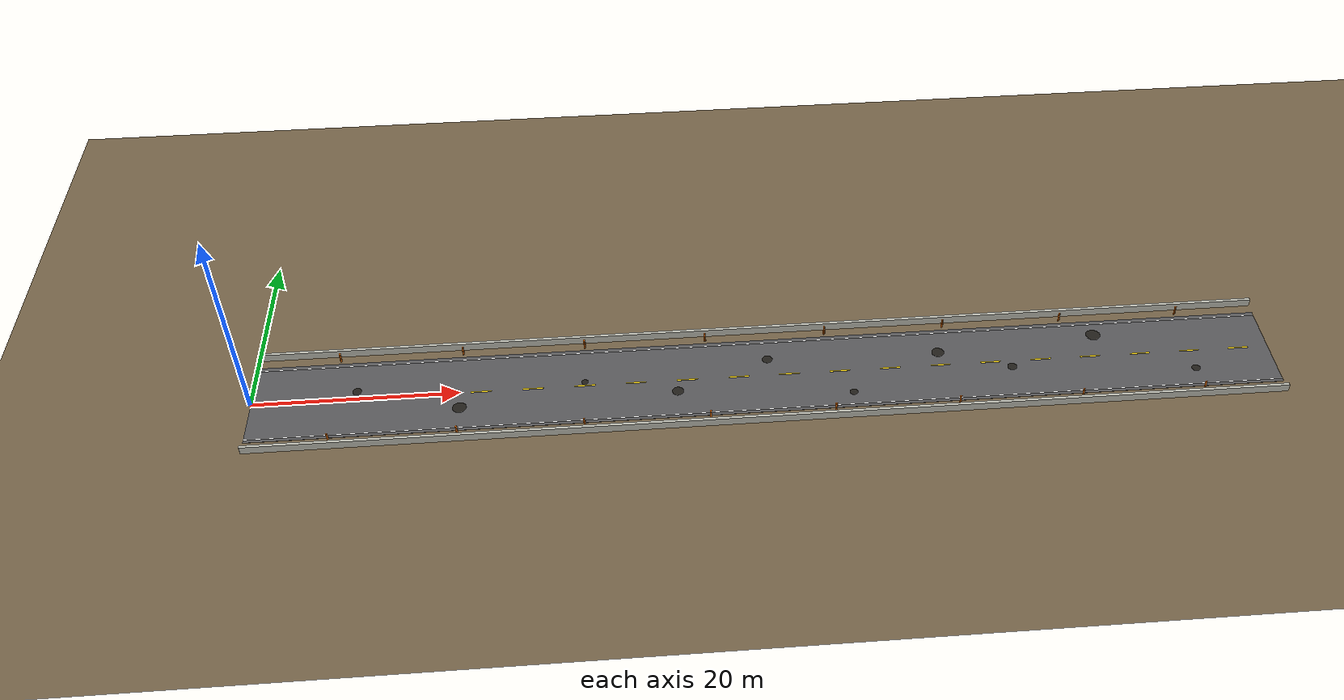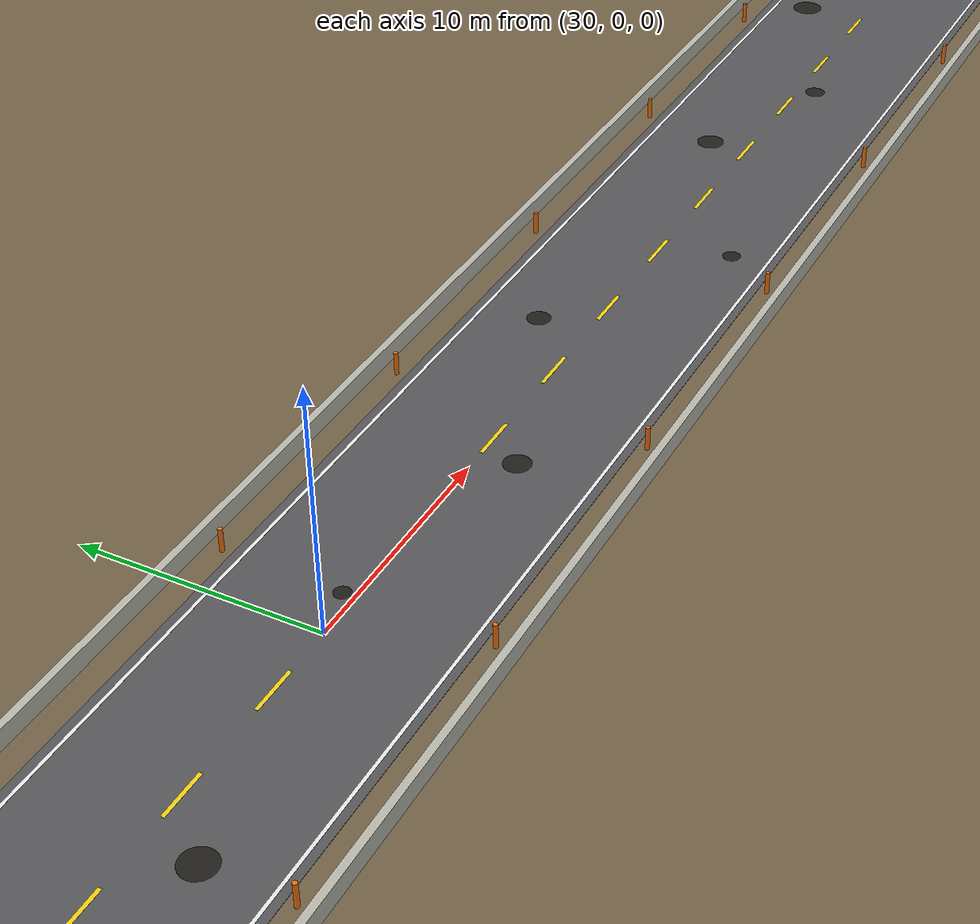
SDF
<?xml version="1.0" ?>
<!-- AUTO-GENERATED by scripts/generate_world.py — do not edit by hand -->
<sdf version="1.6">
  <world name="pothole_road">

    <!-- GPS origin: New Delhi, India -->
    <spherical_coordinates>
      <surface_model>EARTH_WGS84</surface_model>
      <latitude_deg>28.6139</latitude_deg>
      <longitude_deg>77.2090</longitude_deg>
      <elevation>216.0</elevation>
      <heading_deg>0</heading_deg>
    </spherical_coordinates>

    <gravity>0 0 -9.81</gravity>

    <physics type="ode">
      <max_step_size>0.002</max_step_size>
      <real_time_factor>1.0</real_time_factor>
      <real_time_update_rate>500</real_time_update_rate>
      <ode>
        <solver>
          <type>quick</type>
          <iters>50</iters>
          <sor>1.3</sor>
        </solver>
        <constraints>
          <cfm>0.001</cfm>
          <erp>0.2</erp>
          <contact_max_correcting_vel>10</contact_max_correcting_vel>
          <contact_surface_layer>0.001</contact_surface_layer>
        </constraints>
      </ode>
    </physics>

    <scene>
      <ambient>0.55 0.55 0.55 1</ambient>
      <background>0.6 0.72 0.85 1</background>
      <shadows>true</shadows>
    </scene>

    <include><uri>model://sun</uri></include>

    <!-- Dirt ground plane -->
    <model name="ground">
      <static>true</static>
      <link name="link">
        <collision name="c">
          <geometry><plane><normal>0 0 1</normal><size>400 400</size></plane></geometry>
          <surface><friction><ode><mu>1.0</mu><mu2>1.0</mu2></ode></friction></surface>
        </collision>
        <visual name="v">
          <geometry><plane><normal>0 0 1</normal><size>400 400</size></plane></geometry>
          <material><ambient>0.35 0.30 0.22 1</ambient><diffuse>0.45 0.38 0.28 1</diffuse></material>
        </visual>
      </link>
    </model>

    <!-- Asphalt road surface: 100m x 10m -->
    <model name="road_surface">
      <static>true</static>
      <pose>50 0 0.01 0 0 0</pose>
      <link name="link">
        <collision name="collision">
          <geometry><box><size>100 10 0.02</size></box></geometry>
        </collision>
        <visual name="visual">
          <geometry><box><size>100 10 0.02</size></box></geometry>
          <material>
            <ambient>0.26 0.26 0.27 1</ambient>
            <diffuse>0.34 0.34 0.35 1</diffuse>
            <specular>0.02 0.02 0.02 1</specular>
          </material>
        </visual>
      </link>
    </model>

    <!-- Lane markings -->
    <model name="lane_dash_0">
      <static>true</static>
      <pose>2.0 0 0.0210 0 0 0</pose>
      <link name="link"><visual name="v">
        <geometry><box><size>2.0 0.16 0.002</size></box></geometry>
        <material><ambient>0.75 0.65 0.05 1</ambient><diffuse>0.95 0.82 0.08 1</diffuse></material>
      </visual></link>
    </model>
    <model name="lane_dash_1">
      <static>true</static>
      <pose>7.0 0 0.0210 0 0 0</pose>
      <link name="link"><visual name="v">
        <geometry><box><size>2.0 0.16 0.002</size></box></geometry>
        <material><ambient>0.75 0.65 0.05 1</ambient><diffuse>0.95 0.82 0.08 1</diffuse></material>
      </visual></link>
    </model>
    <model name="lane_dash_2">
      <static>true</static>
      <pose>12.0 0 0.0210 0 0 0</pose>
      <link name="link"><visual name="v">
        <geometry><box><size>2.0 0.16 0.002</size></box></geometry>
        <material><ambient>0.75 0.65 0.05 1</ambient><diffuse>0.95 0.82 0.08 1</diffuse></material>
      </visual></link>
    </model>
    <model name="lane_dash_3">
      <static>true</static>
      <pose>17.0 0 0.0210 0 0 0</pose>
      <link name="link"><visual name="v">
        <geometry><box><size>2.0 0.16 0.002</size></box></geometry>
        <material><ambient>0.75 0.65 0.05 1</ambient><diffuse>0.95 0.82 0.08 1</diffuse></material>
      </visual></link>
    </model>
    <model name="lane_dash_4">
      <static>true</static>
      <pose>22.0 0 0.0210 0 0 0</pose>
      <link name="link"><visual name="v">
        <geometry><box><size>2.0 0.16 0.002</size></box></geometry>
        <material><ambient>0.75 0.65 0.05 1</ambient><diffuse>0.95 0.82 0.08 1</diffuse></material>
      </visual></link>
    </model>
    <model name="lane_dash_5">
      <static>true</static>
      <pose>27.0 0 0.0210 0 0 0</pose>
      <link name="link"><visual name="v">
        <geometry><box><size>2.0 0.16 0.002</size></box></geometry>
        <material><ambient>0.75 0.65 0.05 1</ambient><diffuse>0.95 0.82 0.08 1</diffuse></material>
      </visual></link>
    </model>
    <model name="lane_dash_6">
      <static>true</static>
      <pose>32.0 0 0.0210 0 0 0</pose>
      <link name="link"><visual name="v">
        <geometry><box><size>2.0 0.16 0.002</size></box></geometry>
        <material><ambient>0.75 0.65 0.05 1</ambient><diffuse>0.95 0.82 0.08 1</diffuse></material>
      </visual></link>
    </model>
    <model name="lane_dash_7">
      <static>true</static>
      <pose>37.0 0 0.0210 0 0 0</pose>
      <link name="link"><visual name="v">
        <geometry><box><size>2.0 0.16 0.002</size></box></geometry>
        <material><ambient>0.75 0.65 0.05 1</ambient><diffuse>0.95 0.82 0.08 1</diffuse></material>
      </visual></link>
    </model>
    <model name="lane_dash_8">
      <static>true</static>
      <pose>42.0 0 0.0210 0 0 0</pose>
      <link name="link"><visual name="v">
        <geometry><box><size>2.0 0.16 0.002</size></box></geometry>
        <material><ambient>0.75 0.65 0.05 1</ambient><diffuse>0.95 0.82 0.08 1</diffuse></material>
      </visual></link>
    </model>
    <model name="lane_dash_9">
      <static>true</static>
      <pose>47.0 0 0.0210 0 0 0</pose>
      <link name="link"><visual name="v">
        <geometry><box><size>2.0 0.16 0.002</size></box></geometry>
        <material><ambient>0.75 0.65 0.05 1</ambient><diffuse>0.95 0.82 0.08 1</diffuse></material>
      </visual></link>
    </model>
    <model name="lane_dash_10">
      <static>true</static>
      <pose>52.0 0 0.0210 0 0 0</pose>
      <link name="link"><visual name="v">
        <geometry><box><size>2.0 0.16 0.002</size></box></geometry>
        <material><ambient>0.75 0.65 0.05 1</ambient><diffuse>0.95 0.82 0.08 1</diffuse></material>
      </visual></link>
    </model>
    <model name="lane_dash_11">
      <static>true</static>
      <pose>57.0 0 0.0210 0 0 0</pose>
      <link name="link"><visual name="v">
        <geometry><box><size>2.0 0.16 0.002</size></box></geometry>
        <material><ambient>0.75 0.65 0.05 1</ambient><diffuse>0.95 0.82 0.08 1</diffuse></material>
      </visual></link>
    </model>
    <model name="lane_dash_12">
      <static>true</static>
      <pose>62.0 0 0.0210 0 0 0</pose>
      <link name="link"><visual name="v">
        <geometry><box><size>2.0 0.16 0.002</size></box></geometry>
        <material><ambient>0.75 0.65 0.05 1</ambient><diffuse>0.95 0.82 0.08 1</diffuse></material>
      </visual></link>
    </model>
    <model name="lane_dash_13">
      <static>true</static>
      <pose>67.0 0 0.0210 0 0 0</pose>
      <link name="link"><visual name="v">
        <geometry><box><size>2.0 0.16 0.002</size></box></geometry>
        <material><ambient>0.75 0.65 0.05 1</ambient><diffuse>0.95 0.82 0.08 1</diffuse></material>
      </visual></link>
    </model>
    <model name="lane_dash_14">
      <static>true</static>
      <pose>72.0 0 0.0210 0 0 0</pose>
      <link name="link"><visual name="v">
        <geometry><box><size>2.0 0.16 0.002</size></box></geometry>
        <material><ambient>0.75 0.65 0.05 1</ambient><diffuse>0.95 0.82 0.08 1</diffuse></material>
      </visual></link>
    </model>
    <model name="lane_dash_15">
      <static>true</static>
      <pose>77.0 0 0.0210 0 0 0</pose>
      <link name="link"><visual name="v">
        <geometry><box><size>2.0 0.16 0.002</size></box></geometry>
        <material><ambient>0.75 0.65 0.05 1</ambient><diffuse>0.95 0.82 0.08 1</diffuse></material>
      </visual></link>
    </model>
    <model name="lane_dash_16">
      <static>true</static>
      <pose>82.0 0 0.0210 0 0 0</pose>
      <link name="link"><visual name="v">
        <geometry><box><size>2.0 0.16 0.002</size></box></geometry>
        <material><ambient>0.75 0.65 0.05 1</ambient><diffuse>0.95 0.82 0.08 1</diffuse></material>
      </visual></link>
    </model>
    <model name="lane_dash_17">
      <static>true</static>
      <pose>87.0 0 0.0210 0 0 0</pose>
      <link name="link"><visual name="v">
        <geometry><box><size>2.0 0.16 0.002</size></box></geometry>
        <material><ambient>0.75 0.65 0.05 1</ambient><diffuse>0.95 0.82 0.08 1</diffuse></material>
      </visual></link>
    </model>
    <model name="lane_dash_18">
      <static>true</static>
      <pose>92.0 0 0.0210 0 0 0</pose>
      <link name="link"><visual name="v">
        <geometry><box><size>2.0 0.16 0.002</size></box></geometry>
        <material><ambient>0.75 0.65 0.05 1</ambient><diffuse>0.95 0.82 0.08 1</diffuse></material>
      </visual></link>
    </model>
    <model name="lane_dash_19">
      <static>true</static>
      <pose>97.0 0 0.0210 0 0 0</pose>
      <link name="link"><visual name="v">
        <geometry><box><size>2.0 0.16 0.002</size></box></geometry>
        <material><ambient>0.75 0.65 0.05 1</ambient><diffuse>0.95 0.82 0.08 1</diffuse></material>
      </visual></link>
    </model>
    <model name="edge_line_l">
      <static>true</static>
      <pose>50 4.6 0.0210 0 0 0</pose>
      <link name="link"><visual name="v">
        <geometry><box><size>100 0.14 0.002</size></box></geometry>
        <material><ambient>0.75 0.75 0.75 1</ambient><diffuse>0.92 0.92 0.92 1</diffuse></material>
      </visual></link>
    </model>
    <model name="edge_line_r">
      <static>true</static>
      <pose>50 -4.6 0.0210 0 0 0</pose>
      <link name="link"><visual name="v">
        <geometry><box><size>100 0.14 0.002</size></box></geometry>
        <material><ambient>0.75 0.75 0.75 1</ambient><diffuse>0.92 0.92 0.92 1</diffuse></material>
      </visual></link>
    </model>

    <!-- Potholes (recessed, with depth) -->
    <model name="pothole_1">
      <static>true</static>
      <pose>10.0 1.0 0.02 0 0 0</pose>
      <link name="link">
      <visual name="floor">
        <pose>0 0 -0.0800 0 0 0</pose>
        <geometry><cylinder><radius>0.400</radius><length>0.004</length></cylinder></geometry>
        <material><ambient>0.03 0.025 0.02 1</ambient><diffuse>0.05 0.04 0.03 1</diffuse><specular>0 0 0 1</specular></material>
      </visual>
      <collision name="floor_c">
        <pose>0 0 -0.0800 0 0 0</pose>
        <geometry><cylinder><radius>0.400</radius><length>0.004</length></cylinder></geometry>
      </collision>
      <visual name="wall_0">
        <pose>0.4000 0.0000 -0.0400 0 0 0.0000</pose>
        <geometry><box><size>0.02 0.1963 0.0800</size></box></geometry>
        <material><ambient>0.06 0.05 0.04 1</ambient><diffuse>0.08 0.07 0.05 1</diffuse></material>
      </visual>
      <visual name="wall_1">
        <pose>0.3696 0.1531 -0.0400 0 0 0.3927</pose>
        <geometry><box><size>0.02 0.1963 0.0800</size></box></geometry>
        <material><ambient>0.06 0.05 0.04 1</ambient><diffuse>0.08 0.07 0.05 1</diffuse></material>
      </visual>
      <visual name="wall_2">
        <pose>0.2828 0.2828 -0.0400 0 0 0.7854</pose>
        <geometry><box><size>0.02 0.1963 0.0800</size></box></geometry>
        <material><ambient>0.06 0.05 0.04 1</ambient><diffuse>0.08 0.07 0.05 1</diffuse></material>
      </visual>
      <visual name="wall_3">
        <pose>0.1531 0.3696 -0.0400 0 0 1.1781</pose>
        <geometry><box><size>0.02 0.1963 0.0800</size></box></geometry>
        <material><ambient>0.06 0.05 0.04 1</ambient><diffuse>0.08 0.07 0.05 1</diffuse></material>
      </visual>
      <visual name="wall_4">
        <pose>0.0000 0.4000 -0.0400 0 0 1.5708</pose>
        <geometry><box><size>0.02 0.1963 0.0800</size></box></geometry>
        <material><ambient>0.06 0.05 0.04 1</ambient><diffuse>0.08 0.07 0.05 1</diffuse></material>
      </visual>
      <visual name="wall_5">
        <pose>-0.1531 0.3696 -0.0400 0 0 1.9635</pose>
        <geometry><box><size>0.02 0.1963 0.0800</size></box></geometry>
        <material><ambient>0.06 0.05 0.04 1</ambient><diffuse>0.08 0.07 0.05 1</diffuse></material>
      </visual>
      <visual name="wall_6">
        <pose>-0.2828 0.2828 -0.0400 0 0 2.3562</pose>
        <geometry><box><size>0.02 0.1963 0.0800</size></box></geometry>
        <material><ambient>0.06 0.05 0.04 1</ambient><diffuse>0.08 0.07 0.05 1</diffuse></material>
      </visual>
      <visual name="wall_7">
        <pose>-0.3696 0.1531 -0.0400 0 0 2.7489</pose>
        <geometry><box><size>0.02 0.1963 0.0800</size></box></geometry>
        <material><ambient>0.06 0.05 0.04 1</ambient><diffuse>0.08 0.07 0.05 1</diffuse></material>
      </visual>
      <visual name="wall_8">
        <pose>-0.4000 0.0000 -0.0400 0 0 3.1416</pose>
        <geometry><box><size>0.02 0.1963 0.0800</size></box></geometry>
        <material><ambient>0.06 0.05 0.04 1</ambient><diffuse>0.08 0.07 0.05 1</diffuse></material>
      </visual>
      <visual name="wall_9">
        <pose>-0.3696 -0.1531 -0.0400 0 0 3.5343</pose>
        <geometry><box><size>0.02 0.1963 0.0800</size></box></geometry>
        <material><ambient>0.06 0.05 0.04 1</ambient><diffuse>0.08 0.07 0.05 1</diffuse></material>
      </visual>
      <visual name="wall_10">
        <pose>-0.2828 -0.2828 -0.0400 0 0 3.9270</pose>
        <geometry><box><size>0.02 0.1963 0.0800</size></box></geometry>
        <material><ambient>0.06 0.05 0.04 1</ambient><diffuse>0.08 0.07 0.05 1</diffuse></material>
      </visual>
      <visual name="wall_11">
        <pose>-0.1531 -0.3696 -0.0400 0 0 4.3197</pose>
        <geometry><box><size>0.02 0.1963 0.0800</size></box></geometry>
        <material><ambient>0.06 0.05 0.04 1</ambient><diffuse>0.08 0.07 0.05 1</diffuse></material>
      </visual>
      <visual name="wall_12">
        <pose>-0.0000 -0.4000 -0.0400 0 0 4.7124</pose>
        <geometry><box><size>0.02 0.1963 0.0800</size></box></geometry>
        <material><ambient>0.06 0.05 0.04 1</ambient><diffuse>0.08 0.07 0.05 1</diffuse></material>
      </visual>
      <visual name="wall_13">
        <pose>0.1531 -0.3696 -0.0400 0 0 5.1051</pose>
        <geometry><box><size>0.02 0.1963 0.0800</size></box></geometry>
        <material><ambient>0.06 0.05 0.04 1</ambient><diffuse>0.08 0.07 0.05 1</diffuse></material>
      </visual>
      <visual name="wall_14">
        <pose>0.2828 -0.2828 -0.0400 0 0 5.4978</pose>
        <geometry><box><size>0.02 0.1963 0.0800</size></box></geometry>
        <material><ambient>0.06 0.05 0.04 1</ambient><diffuse>0.08 0.07 0.05 1</diffuse></material>
      </visual>
      <visual name="wall_15">
        <pose>0.3696 -0.1531 -0.0400 0 0 5.8905</pose>
        <geometry><box><size>0.02 0.1963 0.0800</size></box></geometry>
        <material><ambient>0.06 0.05 0.04 1</ambient><diffuse>0.08 0.07 0.05 1</diffuse></material>
      </visual>
      <visual name="rim">
        <pose>0 0 0.0025 0 0 0</pose>
        <geometry><cylinder><radius>0.448</radius><length>0.003</length></cylinder></geometry>
        <material><ambient>0.10 0.09 0.08 1</ambient><diffuse>0.13 0.12 0.10 1</diffuse></material>
      </visual>
      </link>
    </model>
    <model name="pothole_2">
      <static>true</static>
      <pose>20.0 -2.0 0.02 0 0 0</pose>
      <link name="link">
      <visual name="floor">
        <pose>0 0 -0.1200 0 0 0</pose>
        <geometry><cylinder><radius>0.600</radius><length>0.004</length></cylinder></geometry>
        <material><ambient>0.03 0.025 0.02 1</ambient><diffuse>0.05 0.04 0.03 1</diffuse><specular>0 0 0 1</specular></material>
      </visual>
      <collision name="floor_c">
        <pose>0 0 -0.1200 0 0 0</pose>
        <geometry><cylinder><radius>0.600</radius><length>0.004</length></cylinder></geometry>
      </collision>
      <visual name="wall_0">
        <pose>0.6000 0.0000 -0.0600 0 0 0.0000</pose>
        <geometry><box><size>0.02 0.2945 0.1200</size></box></geometry>
        <material><ambient>0.06 0.05 0.04 1</ambient><diffuse>0.08 0.07 0.05 1</diffuse></material>
      </visual>
      <visual name="wall_1">
        <pose>0.5543 0.2296 -0.0600 0 0 0.3927</pose>
        <geometry><box><size>0.02 0.2945 0.1200</size></box></geometry>
        <material><ambient>0.06 0.05 0.04 1</ambient><diffuse>0.08 0.07 0.05 1</diffuse></material>
      </visual>
      <visual name="wall_2">
        <pose>0.4243 0.4243 -0.0600 0 0 0.7854</pose>
        <geometry><box><size>0.02 0.2945 0.1200</size></box></geometry>
        <material><ambient>0.06 0.05 0.04 1</ambient><diffuse>0.08 0.07 0.05 1</diffuse></material>
      </visual>
      <visual name="wall_3">
        <pose>0.2296 0.5543 -0.0600 0 0 1.1781</pose>
        <geometry><box><size>0.02 0.2945 0.1200</size></box></geometry>
        <material><ambient>0.06 0.05 0.04 1</ambient><diffuse>0.08 0.07 0.05 1</diffuse></material>
      </visual>
      <visual name="wall_4">
        <pose>0.0000 0.6000 -0.0600 0 0 1.5708</pose>
        <geometry><box><size>0.02 0.2945 0.1200</size></box></geometry>
        <material><ambient>0.06 0.05 0.04 1</ambient><diffuse>0.08 0.07 0.05 1</diffuse></material>
      </visual>
      <visual name="wall_5">
        <pose>-0.2296 0.5543 -0.0600 0 0 1.9635</pose>
        <geometry><box><size>0.02 0.2945 0.1200</size></box></geometry>
        <material><ambient>0.06 0.05 0.04 1</ambient><diffuse>0.08 0.07 0.05 1</diffuse></material>
      </visual>
      <visual name="wall_6">
        <pose>-0.4243 0.4243 -0.0600 0 0 2.3562</pose>
        <geometry><box><size>0.02 0.2945 0.1200</size></box></geometry>
        <material><ambient>0.06 0.05 0.04 1</ambient><diffuse>0.08 0.07 0.05 1</diffuse></material>
      </visual>
      <visual name="wall_7">
        <pose>-0.5543 0.2296 -0.0600 0 0 2.7489</pose>
        <geometry><box><size>0.02 0.2945 0.1200</size></box></geometry>
        <material><ambient>0.06 0.05 0.04 1</ambient><diffuse>0.08 0.07 0.05 1</diffuse></material>
      </visual>
      <visual name="wall_8">
        <pose>-0.6000 0.0000 -0.0600 0 0 3.1416</pose>
        <geometry><box><size>0.02 0.2945 0.1200</size></box></geometry>
        <material><ambient>0.06 0.05 0.04 1</ambient><diffuse>0.08 0.07 0.05 1</diffuse></material>
      </visual>
      <visual name="wall_9">
        <pose>-0.5543 -0.2296 -0.0600 0 0 3.5343</pose>
        <geometry><box><size>0.02 0.2945 0.1200</size></box></geometry>
        <material><ambient>0.06 0.05 0.04 1</ambient><diffuse>0.08 0.07 0.05 1</diffuse></material>
      </visual>
      <visual name="wall_10">
        <pose>-0.4243 -0.4243 -0.0600 0 0 3.9270</pose>
        <geometry><box><size>0.02 0.2945 0.1200</size></box></geometry>
        <material><ambient>0.06 0.05 0.04 1</ambient><diffuse>0.08 0.07 0.05 1</diffuse></material>
      </visual>
      <visual name="wall_11">
        <pose>-0.2296 -0.5543 -0.0600 0 0 4.3197</pose>
        <geometry><box><size>0.02 0.2945 0.1200</size></box></geometry>
        <material><ambient>0.06 0.05 0.04 1</ambient><diffuse>0.08 0.07 0.05 1</diffuse></material>
      </visual>
      <visual name="wall_12">
        <pose>-0.0000 -0.6000 -0.0600 0 0 4.7124</pose>
        <geometry><box><size>0.02 0.2945 0.1200</size></box></geometry>
        <material><ambient>0.06 0.05 0.04 1</ambient><diffuse>0.08 0.07 0.05 1</diffuse></material>
      </visual>
      <visual name="wall_13">
        <pose>0.2296 -0.5543 -0.0600 0 0 5.1051</pose>
        <geometry><box><size>0.02 0.2945 0.1200</size></box></geometry>
        <material><ambient>0.06 0.05 0.04 1</ambient><diffuse>0.08 0.07 0.05 1</diffuse></material>
      </visual>
      <visual name="wall_14">
        <pose>0.4243 -0.4243 -0.0600 0 0 5.4978</pose>
        <geometry><box><size>0.02 0.2945 0.1200</size></box></geometry>
        <material><ambient>0.06 0.05 0.04 1</ambient><diffuse>0.08 0.07 0.05 1</diffuse></material>
      </visual>
      <visual name="wall_15">
        <pose>0.5543 -0.2296 -0.0600 0 0 5.8905</pose>
        <geometry><box><size>0.02 0.2945 0.1200</size></box></geometry>
        <material><ambient>0.06 0.05 0.04 1</ambient><diffuse>0.08 0.07 0.05 1</diffuse></material>
      </visual>
      <visual name="rim">
        <pose>0 0 0.0025 0 0 0</pose>
        <geometry><cylinder><radius>0.672</radius><length>0.003</length></cylinder></geometry>
        <material><ambient>0.10 0.09 0.08 1</ambient><diffuse>0.13 0.12 0.10 1</diffuse></material>
      </visual>
      </link>
    </model>
    <model name="pothole_3">
      <static>true</static>
      <pose>32.0 0.5 0.02 0 0 0</pose>
      <link name="link">
      <visual name="floor">
        <pose>0 0 -0.0500 0 0 0</pose>
        <geometry><cylinder><radius>0.300</radius><length>0.004</length></cylinder></geometry>
        <material><ambient>0.03 0.025 0.02 1</ambient><diffuse>0.05 0.04 0.03 1</diffuse><specular>0 0 0 1</specular></material>
      </visual>
      <collision name="floor_c">
        <pose>0 0 -0.0500 0 0 0</pose>
        <geometry><cylinder><radius>0.300</radius><length>0.004</length></cylinder></geometry>
      </collision>
      <visual name="wall_0">
        <pose>0.3000 0.0000 -0.0250 0 0 0.0000</pose>
        <geometry><box><size>0.02 0.1473 0.0500</size></box></geometry>
        <material><ambient>0.06 0.05 0.04 1</ambient><diffuse>0.08 0.07 0.05 1</diffuse></material>
      </visual>
      <visual name="wall_1">
        <pose>0.2772 0.1148 -0.0250 0 0 0.3927</pose>
        <geometry><box><size>0.02 0.1473 0.0500</size></box></geometry>
        <material><ambient>0.06 0.05 0.04 1</ambient><diffuse>0.08 0.07 0.05 1</diffuse></material>
      </visual>
      <visual name="wall_2">
        <pose>0.2121 0.2121 -0.0250 0 0 0.7854</pose>
        <geometry><box><size>0.02 0.1473 0.0500</size></box></geometry>
        <material><ambient>0.06 0.05 0.04 1</ambient><diffuse>0.08 0.07 0.05 1</diffuse></material>
      </visual>
      <visual name="wall_3">
        <pose>0.1148 0.2772 -0.0250 0 0 1.1781</pose>
        <geometry><box><size>0.02 0.1473 0.0500</size></box></geometry>
        <material><ambient>0.06 0.05 0.04 1</ambient><diffuse>0.08 0.07 0.05 1</diffuse></material>
      </visual>
      <visual name="wall_4">
        <pose>0.0000 0.3000 -0.0250 0 0 1.5708</pose>
        <geometry><box><size>0.02 0.1473 0.0500</size></box></geometry>
        <material><ambient>0.06 0.05 0.04 1</ambient><diffuse>0.08 0.07 0.05 1</diffuse></material>
      </visual>
      <visual name="wall_5">
        <pose>-0.1148 0.2772 -0.0250 0 0 1.9635</pose>
        <geometry><box><size>0.02 0.1473 0.0500</size></box></geometry>
        <material><ambient>0.06 0.05 0.04 1</ambient><diffuse>0.08 0.07 0.05 1</diffuse></material>
      </visual>
      <visual name="wall_6">
        <pose>-0.2121 0.2121 -0.0250 0 0 2.3562</pose>
        <geometry><box><size>0.02 0.1473 0.0500</size></box></geometry>
        <material><ambient>0.06 0.05 0.04 1</ambient><diffuse>0.08 0.07 0.05 1</diffuse></material>
      </visual>
      <visual name="wall_7">
        <pose>-0.2772 0.1148 -0.0250 0 0 2.7489</pose>
        <geometry><box><size>0.02 0.1473 0.0500</size></box></geometry>
        <material><ambient>0.06 0.05 0.04 1</ambient><diffuse>0.08 0.07 0.05 1</diffuse></material>
      </visual>
      <visual name="wall_8">
        <pose>-0.3000 0.0000 -0.0250 0 0 3.1416</pose>
        <geometry><box><size>0.02 0.1473 0.0500</size></box></geometry>
        <material><ambient>0.06 0.05 0.04 1</ambient><diffuse>0.08 0.07 0.05 1</diffuse></material>
      </visual>
      <visual name="wall_9">
        <pose>-0.2772 -0.1148 -0.0250 0 0 3.5343</pose>
        <geometry><box><size>0.02 0.1473 0.0500</size></box></geometry>
        <material><ambient>0.06 0.05 0.04 1</ambient><diffuse>0.08 0.07 0.05 1</diffuse></material>
      </visual>
      <visual name="wall_10">
        <pose>-0.2121 -0.2121 -0.0250 0 0 3.9270</pose>
        <geometry><box><size>0.02 0.1473 0.0500</size></box></geometry>
        <material><ambient>0.06 0.05 0.04 1</ambient><diffuse>0.08 0.07 0.05 1</diffuse></material>
      </visual>
      <visual name="wall_11">
        <pose>-0.1148 -0.2772 -0.0250 0 0 4.3197</pose>
        <geometry><box><size>0.02 0.1473 0.0500</size></box></geometry>
        <material><ambient>0.06 0.05 0.04 1</ambient><diffuse>0.08 0.07 0.05 1</diffuse></material>
      </visual>
      <visual name="wall_12">
        <pose>-0.0000 -0.3000 -0.0250 0 0 4.7124</pose>
        <geometry><box><size>0.02 0.1473 0.0500</size></box></geometry>
        <material><ambient>0.06 0.05 0.04 1</ambient><diffuse>0.08 0.07 0.05 1</diffuse></material>
      </visual>
      <visual name="wall_13">
        <pose>0.1148 -0.2772 -0.0250 0 0 5.1051</pose>
        <geometry><box><size>0.02 0.1473 0.0500</size></box></geometry>
        <material><ambient>0.06 0.05 0.04 1</ambient><diffuse>0.08 0.07 0.05 1</diffuse></material>
      </visual>
      <visual name="wall_14">
        <pose>0.2121 -0.2121 -0.0250 0 0 5.4978</pose>
        <geometry><box><size>0.02 0.1473 0.0500</size></box></geometry>
        <material><ambient>0.06 0.05 0.04 1</ambient><diffuse>0.08 0.07 0.05 1</diffuse></material>
      </visual>
      <visual name="wall_15">
        <pose>0.2772 -0.1148 -0.0250 0 0 5.8905</pose>
        <geometry><box><size>0.02 0.1473 0.0500</size></box></geometry>
        <material><ambient>0.06 0.05 0.04 1</ambient><diffuse>0.08 0.07 0.05 1</diffuse></material>
      </visual>
      <visual name="rim">
        <pose>0 0 0.0025 0 0 0</pose>
        <geometry><cylinder><radius>0.336</radius><length>0.003</length></cylinder></geometry>
        <material><ambient>0.10 0.09 0.08 1</ambient><diffuse>0.13 0.12 0.10 1</diffuse></material>
      </visual>
      </link>
    </model>
    <model name="pothole_4">
      <static>true</static>
      <pose>41.0 -1.5 0.02 0 0 0</pose>
      <link name="link">
      <visual name="floor">
        <pose>0 0 -0.1000 0 0 0</pose>
        <geometry><cylinder><radius>0.500</radius><length>0.004</length></cylinder></geometry>
        <material><ambient>0.03 0.025 0.02 1</ambient><diffuse>0.05 0.04 0.03 1</diffuse><specular>0 0 0 1</specular></material>
      </visual>
      <collision name="floor_c">
        <pose>0 0 -0.1000 0 0 0</pose>
        <geometry><cylinder><radius>0.500</radius><length>0.004</length></cylinder></geometry>
      </collision>
      <visual name="wall_0">
        <pose>0.5000 0.0000 -0.0500 0 0 0.0000</pose>
        <geometry><box><size>0.02 0.2454 0.1000</size></box></geometry>
        <material><ambient>0.06 0.05 0.04 1</ambient><diffuse>0.08 0.07 0.05 1</diffuse></material>
      </visual>
      <visual name="wall_1">
        <pose>0.4619 0.1913 -0.0500 0 0 0.3927</pose>
        <geometry><box><size>0.02 0.2454 0.1000</size></box></geometry>
        <material><ambient>0.06 0.05 0.04 1</ambient><diffuse>0.08 0.07 0.05 1</diffuse></material>
      </visual>
      <visual name="wall_2">
        <pose>0.3536 0.3536 -0.0500 0 0 0.7854</pose>
        <geometry><box><size>0.02 0.2454 0.1000</size></box></geometry>
        <material><ambient>0.06 0.05 0.04 1</ambient><diffuse>0.08 0.07 0.05 1</diffuse></material>
      </visual>
      <visual name="wall_3">
        <pose>0.1913 0.4619 -0.0500 0 0 1.1781</pose>
        <geometry><box><size>0.02 0.2454 0.1000</size></box></geometry>
        <material><ambient>0.06 0.05 0.04 1</ambient><diffuse>0.08 0.07 0.05 1</diffuse></material>
      </visual>
      <visual name="wall_4">
        <pose>0.0000 0.5000 -0.0500 0 0 1.5708</pose>
        <geometry><box><size>0.02 0.2454 0.1000</size></box></geometry>
        <material><ambient>0.06 0.05 0.04 1</ambient><diffuse>0.08 0.07 0.05 1</diffuse></material>
      </visual>
      <visual name="wall_5">
        <pose>-0.1913 0.4619 -0.0500 0 0 1.9635</pose>
        <geometry><box><size>0.02 0.2454 0.1000</size></box></geometry>
        <material><ambient>0.06 0.05 0.04 1</ambient><diffuse>0.08 0.07 0.05 1</diffuse></material>
      </visual>
      <visual name="wall_6">
        <pose>-0.3536 0.3536 -0.0500 0 0 2.3562</pose>
        <geometry><box><size>0.02 0.2454 0.1000</size></box></geometry>
        <material><ambient>0.06 0.05 0.04 1</ambient><diffuse>0.08 0.07 0.05 1</diffuse></material>
      </visual>
      <visual name="wall_7">
        <pose>-0.4619 0.1913 -0.0500 0 0 2.7489</pose>
        <geometry><box><size>0.02 0.2454 0.1000</size></box></geometry>
        <material><ambient>0.06 0.05 0.04 1</ambient><diffuse>0.08 0.07 0.05 1</diffuse></material>
      </visual>
      <visual name="wall_8">
        <pose>-0.5000 0.0000 -0.0500 0 0 3.1416</pose>
        <geometry><box><size>0.02 0.2454 0.1000</size></box></geometry>
        <material><ambient>0.06 0.05 0.04 1</ambient><diffuse>0.08 0.07 0.05 1</diffuse></material>
      </visual>
      <visual name="wall_9">
        <pose>-0.4619 -0.1913 -0.0500 0 0 3.5343</pose>
        <geometry><box><size>0.02 0.2454 0.1000</size></box></geometry>
        <material><ambient>0.06 0.05 0.04 1</ambient><diffuse>0.08 0.07 0.05 1</diffuse></material>
      </visual>
      <visual name="wall_10">
        <pose>-0.3536 -0.3536 -0.0500 0 0 3.9270</pose>
        <geometry><box><size>0.02 0.2454 0.1000</size></box></geometry>
        <material><ambient>0.06 0.05 0.04 1</ambient><diffuse>0.08 0.07 0.05 1</diffuse></material>
      </visual>
      <visual name="wall_11">
        <pose>-0.1913 -0.4619 -0.0500 0 0 4.3197</pose>
        <geometry><box><size>0.02 0.2454 0.1000</size></box></geometry>
        <material><ambient>0.06 0.05 0.04 1</ambient><diffuse>0.08 0.07 0.05 1</diffuse></material>
      </visual>
      <visual name="wall_12">
        <pose>-0.0000 -0.5000 -0.0500 0 0 4.7124</pose>
        <geometry><box><size>0.02 0.2454 0.1000</size></box></geometry>
        <material><ambient>0.06 0.05 0.04 1</ambient><diffuse>0.08 0.07 0.05 1</diffuse></material>
      </visual>
      <visual name="wall_13">
        <pose>0.1913 -0.4619 -0.0500 0 0 5.1051</pose>
        <geometry><box><size>0.02 0.2454 0.1000</size></box></geometry>
        <material><ambient>0.06 0.05 0.04 1</ambient><diffuse>0.08 0.07 0.05 1</diffuse></material>
      </visual>
      <visual name="wall_14">
        <pose>0.3536 -0.3536 -0.0500 0 0 5.4978</pose>
        <geometry><box><size>0.02 0.2454 0.1000</size></box></geometry>
        <material><ambient>0.06 0.05 0.04 1</ambient><diffuse>0.08 0.07 0.05 1</diffuse></material>
      </visual>
      <visual name="wall_15">
        <pose>0.4619 -0.1913 -0.0500 0 0 5.8905</pose>
        <geometry><box><size>0.02 0.2454 0.1000</size></box></geometry>
        <material><ambient>0.06 0.05 0.04 1</ambient><diffuse>0.08 0.07 0.05 1</diffuse></material>
      </visual>
      <visual name="rim">
        <pose>0 0 0.0025 0 0 0</pose>
        <geometry><cylinder><radius>0.560</radius><length>0.003</length></cylinder></geometry>
        <material><ambient>0.10 0.09 0.08 1</ambient><diffuse>0.13 0.12 0.10 1</diffuse></material>
      </visual>
      </link>
    </model>
    <model name="pothole_5">
      <static>true</static>
      <pose>50.0 2.2 0.02 0 0 0</pose>
      <link name="link">
      <visual name="floor">
        <pose>0 0 -0.0900 0 0 0</pose>
        <geometry><cylinder><radius>0.450</radius><length>0.004</length></cylinder></geometry>
        <material><ambient>0.03 0.025 0.02 1</ambient><diffuse>0.05 0.04 0.03 1</diffuse><specular>0 0 0 1</specular></material>
      </visual>
      <collision name="floor_c">
        <pose>0 0 -0.0900 0 0 0</pose>
        <geometry><cylinder><radius>0.450</radius><length>0.004</length></cylinder></geometry>
      </collision>
      <visual name="wall_0">
        <pose>0.4500 0.0000 -0.0450 0 0 0.0000</pose>
        <geometry><box><size>0.02 0.2209 0.0900</size></box></geometry>
        <material><ambient>0.06 0.05 0.04 1</ambient><diffuse>0.08 0.07 0.05 1</diffuse></material>
      </visual>
      <visual name="wall_1">
        <pose>0.4157 0.1722 -0.0450 0 0 0.3927</pose>
        <geometry><box><size>0.02 0.2209 0.0900</size></box></geometry>
        <material><ambient>0.06 0.05 0.04 1</ambient><diffuse>0.08 0.07 0.05 1</diffuse></material>
      </visual>
      <visual name="wall_2">
        <pose>0.3182 0.3182 -0.0450 0 0 0.7854</pose>
        <geometry><box><size>0.02 0.2209 0.0900</size></box></geometry>
        <material><ambient>0.06 0.05 0.04 1</ambient><diffuse>0.08 0.07 0.05 1</diffuse></material>
      </visual>
      <visual name="wall_3">
        <pose>0.1722 0.4157 -0.0450 0 0 1.1781</pose>
        <geometry><box><size>0.02 0.2209 0.0900</size></box></geometry>
        <material><ambient>0.06 0.05 0.04 1</ambient><diffuse>0.08 0.07 0.05 1</diffuse></material>
      </visual>
      <visual name="wall_4">
        <pose>0.0000 0.4500 -0.0450 0 0 1.5708</pose>
        <geometry><box><size>0.02 0.2209 0.0900</size></box></geometry>
        <material><ambient>0.06 0.05 0.04 1</ambient><diffuse>0.08 0.07 0.05 1</diffuse></material>
      </visual>
      <visual name="wall_5">
        <pose>-0.1722 0.4157 -0.0450 0 0 1.9635</pose>
        <geometry><box><size>0.02 0.2209 0.0900</size></box></geometry>
        <material><ambient>0.06 0.05 0.04 1</ambient><diffuse>0.08 0.07 0.05 1</diffuse></material>
      </visual>
      <visual name="wall_6">
        <pose>-0.3182 0.3182 -0.0450 0 0 2.3562</pose>
        <geometry><box><size>0.02 0.2209 0.0900</size></box></geometry>
        <material><ambient>0.06 0.05 0.04 1</ambient><diffuse>0.08 0.07 0.05 1</diffuse></material>
      </visual>
      <visual name="wall_7">
        <pose>-0.4157 0.1722 -0.0450 0 0 2.7489</pose>
        <geometry><box><size>0.02 0.2209 0.0900</size></box></geometry>
        <material><ambient>0.06 0.05 0.04 1</ambient><diffuse>0.08 0.07 0.05 1</diffuse></material>
      </visual>
      <visual name="wall_8">
        <pose>-0.4500 0.0000 -0.0450 0 0 3.1416</pose>
        <geometry><box><size>0.02 0.2209 0.0900</size></box></geometry>
        <material><ambient>0.06 0.05 0.04 1</ambient><diffuse>0.08 0.07 0.05 1</diffuse></material>
      </visual>
      <visual name="wall_9">
        <pose>-0.4157 -0.1722 -0.0450 0 0 3.5343</pose>
        <geometry><box><size>0.02 0.2209 0.0900</size></box></geometry>
        <material><ambient>0.06 0.05 0.04 1</ambient><diffuse>0.08 0.07 0.05 1</diffuse></material>
      </visual>
      <visual name="wall_10">
        <pose>-0.3182 -0.3182 -0.0450 0 0 3.9270</pose>
        <geometry><box><size>0.02 0.2209 0.0900</size></box></geometry>
        <material><ambient>0.06 0.05 0.04 1</ambient><diffuse>0.08 0.07 0.05 1</diffuse></material>
      </visual>
      <visual name="wall_11">
        <pose>-0.1722 -0.4157 -0.0450 0 0 4.3197</pose>
        <geometry><box><size>0.02 0.2209 0.0900</size></box></geometry>
        <material><ambient>0.06 0.05 0.04 1</ambient><diffuse>0.08 0.07 0.05 1</diffuse></material>
      </visual>
      <visual name="wall_12">
        <pose>-0.0000 -0.4500 -0.0450 0 0 4.7124</pose>
        <geometry><box><size>0.02 0.2209 0.0900</size></box></geometry>
        <material><ambient>0.06 0.05 0.04 1</ambient><diffuse>0.08 0.07 0.05 1</diffuse></material>
      </visual>
      <visual name="wall_13">
        <pose>0.1722 -0.4157 -0.0450 0 0 5.1051</pose>
        <geometry><box><size>0.02 0.2209 0.0900</size></box></geometry>
        <material><ambient>0.06 0.05 0.04 1</ambient><diffuse>0.08 0.07 0.05 1</diffuse></material>
      </visual>
      <visual name="wall_14">
        <pose>0.3182 -0.3182 -0.0450 0 0 5.4978</pose>
        <geometry><box><size>0.02 0.2209 0.0900</size></box></geometry>
        <material><ambient>0.06 0.05 0.04 1</ambient><diffuse>0.08 0.07 0.05 1</diffuse></material>
      </visual>
      <visual name="wall_15">
        <pose>0.4157 -0.1722 -0.0450 0 0 5.8905</pose>
        <geometry><box><size>0.02 0.2209 0.0900</size></box></geometry>
        <material><ambient>0.06 0.05 0.04 1</ambient><diffuse>0.08 0.07 0.05 1</diffuse></material>
      </visual>
      <visual name="rim">
        <pose>0 0 0.0025 0 0 0</pose>
        <geometry><cylinder><radius>0.504</radius><length>0.003</length></cylinder></geometry>
        <material><ambient>0.10 0.09 0.08 1</ambient><diffuse>0.13 0.12 0.10 1</diffuse></material>
      </visual>
      </link>
    </model>
    <model name="pothole_6">
      <static>true</static>
      <pose>58.0 -3.0 0.02 0 0 0</pose>
      <link name="link">
      <visual name="floor">
        <pose>0 0 -0.0600 0 0 0</pose>
        <geometry><cylinder><radius>0.350</radius><length>0.004</length></cylinder></geometry>
        <material><ambient>0.03 0.025 0.02 1</ambient><diffuse>0.05 0.04 0.03 1</diffuse><specular>0 0 0 1</specular></material>
      </visual>
      <collision name="floor_c">
        <pose>0 0 -0.0600 0 0 0</pose>
        <geometry><cylinder><radius>0.350</radius><length>0.004</length></cylinder></geometry>
      </collision>
      <visual name="wall_0">
        <pose>0.3500 0.0000 -0.0300 0 0 0.0000</pose>
        <geometry><box><size>0.02 0.1718 0.0600</size></box></geometry>
        <material><ambient>0.06 0.05 0.04 1</ambient><diffuse>0.08 0.07 0.05 1</diffuse></material>
      </visual>
      <visual name="wall_1">
        <pose>0.3234 0.1339 -0.0300 0 0 0.3927</pose>
        <geometry><box><size>0.02 0.1718 0.0600</size></box></geometry>
        <material><ambient>0.06 0.05 0.04 1</ambient><diffuse>0.08 0.07 0.05 1</diffuse></material>
      </visual>
      <visual name="wall_2">
        <pose>0.2475 0.2475 -0.0300 0 0 0.7854</pose>
        <geometry><box><size>0.02 0.1718 0.0600</size></box></geometry>
        <material><ambient>0.06 0.05 0.04 1</ambient><diffuse>0.08 0.07 0.05 1</diffuse></material>
      </visual>
      <visual name="wall_3">
        <pose>0.1339 0.3234 -0.0300 0 0 1.1781</pose>
        <geometry><box><size>0.02 0.1718 0.0600</size></box></geometry>
        <material><ambient>0.06 0.05 0.04 1</ambient><diffuse>0.08 0.07 0.05 1</diffuse></material>
      </visual>
      <visual name="wall_4">
        <pose>0.0000 0.3500 -0.0300 0 0 1.5708</pose>
        <geometry><box><size>0.02 0.1718 0.0600</size></box></geometry>
        <material><ambient>0.06 0.05 0.04 1</ambient><diffuse>0.08 0.07 0.05 1</diffuse></material>
      </visual>
      <visual name="wall_5">
        <pose>-0.1339 0.3234 -0.0300 0 0 1.9635</pose>
        <geometry><box><size>0.02 0.1718 0.0600</size></box></geometry>
        <material><ambient>0.06 0.05 0.04 1</ambient><diffuse>0.08 0.07 0.05 1</diffuse></material>
      </visual>
      <visual name="wall_6">
        <pose>-0.2475 0.2475 -0.0300 0 0 2.3562</pose>
        <geometry><box><size>0.02 0.1718 0.0600</size></box></geometry>
        <material><ambient>0.06 0.05 0.04 1</ambient><diffuse>0.08 0.07 0.05 1</diffuse></material>
      </visual>
      <visual name="wall_7">
        <pose>-0.3234 0.1339 -0.0300 0 0 2.7489</pose>
        <geometry><box><size>0.02 0.1718 0.0600</size></box></geometry>
        <material><ambient>0.06 0.05 0.04 1</ambient><diffuse>0.08 0.07 0.05 1</diffuse></material>
      </visual>
      <visual name="wall_8">
        <pose>-0.3500 0.0000 -0.0300 0 0 3.1416</pose>
        <geometry><box><size>0.02 0.1718 0.0600</size></box></geometry>
        <material><ambient>0.06 0.05 0.04 1</ambient><diffuse>0.08 0.07 0.05 1</diffuse></material>
      </visual>
      <visual name="wall_9">
        <pose>-0.3234 -0.1339 -0.0300 0 0 3.5343</pose>
        <geometry><box><size>0.02 0.1718 0.0600</size></box></geometry>
        <material><ambient>0.06 0.05 0.04 1</ambient><diffuse>0.08 0.07 0.05 1</diffuse></material>
      </visual>
      <visual name="wall_10">
        <pose>-0.2475 -0.2475 -0.0300 0 0 3.9270</pose>
        <geometry><box><size>0.02 0.1718 0.0600</size></box></geometry>
        <material><ambient>0.06 0.05 0.04 1</ambient><diffuse>0.08 0.07 0.05 1</diffuse></material>
      </visual>
      <visual name="wall_11">
        <pose>-0.1339 -0.3234 -0.0300 0 0 4.3197</pose>
        <geometry><box><size>0.02 0.1718 0.0600</size></box></geometry>
        <material><ambient>0.06 0.05 0.04 1</ambient><diffuse>0.08 0.07 0.05 1</diffuse></material>
      </visual>
      <visual name="wall_12">
        <pose>-0.0000 -0.3500 -0.0300 0 0 4.7124</pose>
        <geometry><box><size>0.02 0.1718 0.0600</size></box></geometry>
        <material><ambient>0.06 0.05 0.04 1</ambient><diffuse>0.08 0.07 0.05 1</diffuse></material>
      </visual>
      <visual name="wall_13">
        <pose>0.1339 -0.3234 -0.0300 0 0 5.1051</pose>
        <geometry><box><size>0.02 0.1718 0.0600</size></box></geometry>
        <material><ambient>0.06 0.05 0.04 1</ambient><diffuse>0.08 0.07 0.05 1</diffuse></material>
      </visual>
      <visual name="wall_14">
        <pose>0.2475 -0.2475 -0.0300 0 0 5.4978</pose>
        <geometry><box><size>0.02 0.1718 0.0600</size></box></geometry>
        <material><ambient>0.06 0.05 0.04 1</ambient><diffuse>0.08 0.07 0.05 1</diffuse></material>
      </visual>
      <visual name="wall_15">
        <pose>0.3234 -0.1339 -0.0300 0 0 5.8905</pose>
        <geometry><box><size>0.02 0.1718 0.0600</size></box></geometry>
        <material><ambient>0.06 0.05 0.04 1</ambient><diffuse>0.08 0.07 0.05 1</diffuse></material>
      </visual>
      <visual name="rim">
        <pose>0 0 0.0025 0 0 0</pose>
        <geometry><cylinder><radius>0.392</radius><length>0.003</length></cylinder></geometry>
        <material><ambient>0.10 0.09 0.08 1</ambient><diffuse>0.13 0.12 0.10 1</diffuse></material>
      </visual>
      </link>
    </model>
    <model name="pothole_7">
      <static>true</static>
      <pose>67.0 1.8 0.02 0 0 0</pose>
      <link name="link">
      <visual name="floor">
        <pose>0 0 -0.1300 0 0 0</pose>
        <geometry><cylinder><radius>0.550</radius><length>0.004</length></cylinder></geometry>
        <material><ambient>0.03 0.025 0.02 1</ambient><diffuse>0.05 0.04 0.03 1</diffuse><specular>0 0 0 1</specular></material>
      </visual>
      <collision name="floor_c">
        <pose>0 0 -0.1300 0 0 0</pose>
        <geometry><cylinder><radius>0.550</radius><length>0.004</length></cylinder></geometry>
      </collision>
      <visual name="wall_0">
        <pose>0.5500 0.0000 -0.0650 0 0 0.0000</pose>
        <geometry><box><size>0.02 0.2700 0.1300</size></box></geometry>
        <material><ambient>0.06 0.05 0.04 1</ambient><diffuse>0.08 0.07 0.05 1</diffuse></material>
      </visual>
      <visual name="wall_1">
        <pose>0.5081 0.2105 -0.0650 0 0 0.3927</pose>
        <geometry><box><size>0.02 0.2700 0.1300</size></box></geometry>
        <material><ambient>0.06 0.05 0.04 1</ambient><diffuse>0.08 0.07 0.05 1</diffuse></material>
      </visual>
      <visual name="wall_2">
        <pose>0.3889 0.3889 -0.0650 0 0 0.7854</pose>
        <geometry><box><size>0.02 0.2700 0.1300</size></box></geometry>
        <material><ambient>0.06 0.05 0.04 1</ambient><diffuse>0.08 0.07 0.05 1</diffuse></material>
      </visual>
      <visual name="wall_3">
        <pose>0.2105 0.5081 -0.0650 0 0 1.1781</pose>
        <geometry><box><size>0.02 0.2700 0.1300</size></box></geometry>
        <material><ambient>0.06 0.05 0.04 1</ambient><diffuse>0.08 0.07 0.05 1</diffuse></material>
      </visual>
      <visual name="wall_4">
        <pose>0.0000 0.5500 -0.0650 0 0 1.5708</pose>
        <geometry><box><size>0.02 0.2700 0.1300</size></box></geometry>
        <material><ambient>0.06 0.05 0.04 1</ambient><diffuse>0.08 0.07 0.05 1</diffuse></material>
      </visual>
      <visual name="wall_5">
        <pose>-0.2105 0.5081 -0.0650 0 0 1.9635</pose>
        <geometry><box><size>0.02 0.2700 0.1300</size></box></geometry>
        <material><ambient>0.06 0.05 0.04 1</ambient><diffuse>0.08 0.07 0.05 1</diffuse></material>
      </visual>
      <visual name="wall_6">
        <pose>-0.3889 0.3889 -0.0650 0 0 2.3562</pose>
        <geometry><box><size>0.02 0.2700 0.1300</size></box></geometry>
        <material><ambient>0.06 0.05 0.04 1</ambient><diffuse>0.08 0.07 0.05 1</diffuse></material>
      </visual>
      <visual name="wall_7">
        <pose>-0.5081 0.2105 -0.0650 0 0 2.7489</pose>
        <geometry><box><size>0.02 0.2700 0.1300</size></box></geometry>
        <material><ambient>0.06 0.05 0.04 1</ambient><diffuse>0.08 0.07 0.05 1</diffuse></material>
      </visual>
      <visual name="wall_8">
        <pose>-0.5500 0.0000 -0.0650 0 0 3.1416</pose>
        <geometry><box><size>0.02 0.2700 0.1300</size></box></geometry>
        <material><ambient>0.06 0.05 0.04 1</ambient><diffuse>0.08 0.07 0.05 1</diffuse></material>
      </visual>
      <visual name="wall_9">
        <pose>-0.5081 -0.2105 -0.0650 0 0 3.5343</pose>
        <geometry><box><size>0.02 0.2700 0.1300</size></box></geometry>
        <material><ambient>0.06 0.05 0.04 1</ambient><diffuse>0.08 0.07 0.05 1</diffuse></material>
      </visual>
      <visual name="wall_10">
        <pose>-0.3889 -0.3889 -0.0650 0 0 3.9270</pose>
        <geometry><box><size>0.02 0.2700 0.1300</size></box></geometry>
        <material><ambient>0.06 0.05 0.04 1</ambient><diffuse>0.08 0.07 0.05 1</diffuse></material>
      </visual>
      <visual name="wall_11">
        <pose>-0.2105 -0.5081 -0.0650 0 0 4.3197</pose>
        <geometry><box><size>0.02 0.2700 0.1300</size></box></geometry>
        <material><ambient>0.06 0.05 0.04 1</ambient><diffuse>0.08 0.07 0.05 1</diffuse></material>
      </visual>
      <visual name="wall_12">
        <pose>-0.0000 -0.5500 -0.0650 0 0 4.7124</pose>
        <geometry><box><size>0.02 0.2700 0.1300</size></box></geometry>
        <material><ambient>0.06 0.05 0.04 1</ambient><diffuse>0.08 0.07 0.05 1</diffuse></material>
      </visual>
      <visual name="wall_13">
        <pose>0.2105 -0.5081 -0.0650 0 0 5.1051</pose>
        <geometry><box><size>0.02 0.2700 0.1300</size></box></geometry>
        <material><ambient>0.06 0.05 0.04 1</ambient><diffuse>0.08 0.07 0.05 1</diffuse></material>
      </visual>
      <visual name="wall_14">
        <pose>0.3889 -0.3889 -0.0650 0 0 5.4978</pose>
        <geometry><box><size>0.02 0.2700 0.1300</size></box></geometry>
        <material><ambient>0.06 0.05 0.04 1</ambient><diffuse>0.08 0.07 0.05 1</diffuse></material>
      </visual>
      <visual name="wall_15">
        <pose>0.5081 -0.2105 -0.0650 0 0 5.8905</pose>
        <geometry><box><size>0.02 0.2700 0.1300</size></box></geometry>
        <material><ambient>0.06 0.05 0.04 1</ambient><diffuse>0.08 0.07 0.05 1</diffuse></material>
      </visual>
      <visual name="rim">
        <pose>0 0 0.0025 0 0 0</pose>
        <geometry><cylinder><radius>0.616</radius><length>0.003</length></cylinder></geometry>
        <material><ambient>0.10 0.09 0.08 1</ambient><diffuse>0.13 0.12 0.10 1</diffuse></material>
      </visual>
      </link>
    </model>
    <model name="pothole_8">
      <static>true</static>
      <pose>74.0 -0.8 0.02 0 0 0</pose>
      <link name="link">
      <visual name="floor">
        <pose>0 0 -0.0700 0 0 0</pose>
        <geometry><cylinder><radius>0.420</radius><length>0.004</length></cylinder></geometry>
        <material><ambient>0.03 0.025 0.02 1</ambient><diffuse>0.05 0.04 0.03 1</diffuse><specular>0 0 0 1</specular></material>
      </visual>
      <collision name="floor_c">
        <pose>0 0 -0.0700 0 0 0</pose>
        <geometry><cylinder><radius>0.420</radius><length>0.004</length></cylinder></geometry>
      </collision>
      <visual name="wall_0">
        <pose>0.4200 0.0000 -0.0350 0 0 0.0000</pose>
        <geometry><box><size>0.02 0.2062 0.0700</size></box></geometry>
        <material><ambient>0.06 0.05 0.04 1</ambient><diffuse>0.08 0.07 0.05 1</diffuse></material>
      </visual>
      <visual name="wall_1">
        <pose>0.3880 0.1607 -0.0350 0 0 0.3927</pose>
        <geometry><box><size>0.02 0.2062 0.0700</size></box></geometry>
        <material><ambient>0.06 0.05 0.04 1</ambient><diffuse>0.08 0.07 0.05 1</diffuse></material>
      </visual>
      <visual name="wall_2">
        <pose>0.2970 0.2970 -0.0350 0 0 0.7854</pose>
        <geometry><box><size>0.02 0.2062 0.0700</size></box></geometry>
        <material><ambient>0.06 0.05 0.04 1</ambient><diffuse>0.08 0.07 0.05 1</diffuse></material>
      </visual>
      <visual name="wall_3">
        <pose>0.1607 0.3880 -0.0350 0 0 1.1781</pose>
        <geometry><box><size>0.02 0.2062 0.0700</size></box></geometry>
        <material><ambient>0.06 0.05 0.04 1</ambient><diffuse>0.08 0.07 0.05 1</diffuse></material>
      </visual>
      <visual name="wall_4">
        <pose>0.0000 0.4200 -0.0350 0 0 1.5708</pose>
        <geometry><box><size>0.02 0.2062 0.0700</size></box></geometry>
        <material><ambient>0.06 0.05 0.04 1</ambient><diffuse>0.08 0.07 0.05 1</diffuse></material>
      </visual>
      <visual name="wall_5">
        <pose>-0.1607 0.3880 -0.0350 0 0 1.9635</pose>
        <geometry><box><size>0.02 0.2062 0.0700</size></box></geometry>
        <material><ambient>0.06 0.05 0.04 1</ambient><diffuse>0.08 0.07 0.05 1</diffuse></material>
      </visual>
      <visual name="wall_6">
        <pose>-0.2970 0.2970 -0.0350 0 0 2.3562</pose>
        <geometry><box><size>0.02 0.2062 0.0700</size></box></geometry>
        <material><ambient>0.06 0.05 0.04 1</ambient><diffuse>0.08 0.07 0.05 1</diffuse></material>
      </visual>
      <visual name="wall_7">
        <pose>-0.3880 0.1607 -0.0350 0 0 2.7489</pose>
        <geometry><box><size>0.02 0.2062 0.0700</size></box></geometry>
        <material><ambient>0.06 0.05 0.04 1</ambient><diffuse>0.08 0.07 0.05 1</diffuse></material>
      </visual>
      <visual name="wall_8">
        <pose>-0.4200 0.0000 -0.0350 0 0 3.1416</pose>
        <geometry><box><size>0.02 0.2062 0.0700</size></box></geometry>
        <material><ambient>0.06 0.05 0.04 1</ambient><diffuse>0.08 0.07 0.05 1</diffuse></material>
      </visual>
      <visual name="wall_9">
        <pose>-0.3880 -0.1607 -0.0350 0 0 3.5343</pose>
        <geometry><box><size>0.02 0.2062 0.0700</size></box></geometry>
        <material><ambient>0.06 0.05 0.04 1</ambient><diffuse>0.08 0.07 0.05 1</diffuse></material>
      </visual>
      <visual name="wall_10">
        <pose>-0.2970 -0.2970 -0.0350 0 0 3.9270</pose>
        <geometry><box><size>0.02 0.2062 0.0700</size></box></geometry>
        <material><ambient>0.06 0.05 0.04 1</ambient><diffuse>0.08 0.07 0.05 1</diffuse></material>
      </visual>
      <visual name="wall_11">
        <pose>-0.1607 -0.3880 -0.0350 0 0 4.3197</pose>
        <geometry><box><size>0.02 0.2062 0.0700</size></box></geometry>
        <material><ambient>0.06 0.05 0.04 1</ambient><diffuse>0.08 0.07 0.05 1</diffuse></material>
      </visual>
      <visual name="wall_12">
        <pose>-0.0000 -0.4200 -0.0350 0 0 4.7124</pose>
        <geometry><box><size>0.02 0.2062 0.0700</size></box></geometry>
        <material><ambient>0.06 0.05 0.04 1</ambient><diffuse>0.08 0.07 0.05 1</diffuse></material>
      </visual>
      <visual name="wall_13">
        <pose>0.1607 -0.3880 -0.0350 0 0 5.1051</pose>
        <geometry><box><size>0.02 0.2062 0.0700</size></box></geometry>
        <material><ambient>0.06 0.05 0.04 1</ambient><diffuse>0.08 0.07 0.05 1</diffuse></material>
      </visual>
      <visual name="wall_14">
        <pose>0.2970 -0.2970 -0.0350 0 0 5.4978</pose>
        <geometry><box><size>0.02 0.2062 0.0700</size></box></geometry>
        <material><ambient>0.06 0.05 0.04 1</ambient><diffuse>0.08 0.07 0.05 1</diffuse></material>
      </visual>
      <visual name="wall_15">
        <pose>0.3880 -0.1607 -0.0350 0 0 5.8905</pose>
        <geometry><box><size>0.02 0.2062 0.0700</size></box></geometry>
        <material><ambient>0.06 0.05 0.04 1</ambient><diffuse>0.08 0.07 0.05 1</diffuse></material>
      </visual>
      <visual name="rim">
        <pose>0 0 0.0025 0 0 0</pose>
        <geometry><cylinder><radius>0.470</radius><length>0.003</length></cylinder></geometry>
        <material><ambient>0.10 0.09 0.08 1</ambient><diffuse>0.13 0.12 0.10 1</diffuse></material>
      </visual>
      </link>
    </model>
    <model name="pothole_9">
      <static>true</static>
      <pose>83.0 3.0 0.02 0 0 0</pose>
      <link name="link">
      <visual name="floor">
        <pose>0 0 -0.1500 0 0 0</pose>
        <geometry><cylinder><radius>0.650</radius><length>0.004</length></cylinder></geometry>
        <material><ambient>0.03 0.025 0.02 1</ambient><diffuse>0.05 0.04 0.03 1</diffuse><specular>0 0 0 1</specular></material>
      </visual>
      <collision name="floor_c">
        <pose>0 0 -0.1500 0 0 0</pose>
        <geometry><cylinder><radius>0.650</radius><length>0.004</length></cylinder></geometry>
      </collision>
      <visual name="wall_0">
        <pose>0.6500 0.0000 -0.0750 0 0 0.0000</pose>
        <geometry><box><size>0.02 0.3191 0.1500</size></box></geometry>
        <material><ambient>0.06 0.05 0.04 1</ambient><diffuse>0.08 0.07 0.05 1</diffuse></material>
      </visual>
      <visual name="wall_1">
        <pose>0.6005 0.2487 -0.0750 0 0 0.3927</pose>
        <geometry><box><size>0.02 0.3191 0.1500</size></box></geometry>
        <material><ambient>0.06 0.05 0.04 1</ambient><diffuse>0.08 0.07 0.05 1</diffuse></material>
      </visual>
      <visual name="wall_2">
        <pose>0.4596 0.4596 -0.0750 0 0 0.7854</pose>
        <geometry><box><size>0.02 0.3191 0.1500</size></box></geometry>
        <material><ambient>0.06 0.05 0.04 1</ambient><diffuse>0.08 0.07 0.05 1</diffuse></material>
      </visual>
      <visual name="wall_3">
        <pose>0.2487 0.6005 -0.0750 0 0 1.1781</pose>
        <geometry><box><size>0.02 0.3191 0.1500</size></box></geometry>
        <material><ambient>0.06 0.05 0.04 1</ambient><diffuse>0.08 0.07 0.05 1</diffuse></material>
      </visual>
      <visual name="wall_4">
        <pose>0.0000 0.6500 -0.0750 0 0 1.5708</pose>
        <geometry><box><size>0.02 0.3191 0.1500</size></box></geometry>
        <material><ambient>0.06 0.05 0.04 1</ambient><diffuse>0.08 0.07 0.05 1</diffuse></material>
      </visual>
      <visual name="wall_5">
        <pose>-0.2487 0.6005 -0.0750 0 0 1.9635</pose>
        <geometry><box><size>0.02 0.3191 0.1500</size></box></geometry>
        <material><ambient>0.06 0.05 0.04 1</ambient><diffuse>0.08 0.07 0.05 1</diffuse></material>
      </visual>
      <visual name="wall_6">
        <pose>-0.4596 0.4596 -0.0750 0 0 2.3562</pose>
        <geometry><box><size>0.02 0.3191 0.1500</size></box></geometry>
        <material><ambient>0.06 0.05 0.04 1</ambient><diffuse>0.08 0.07 0.05 1</diffuse></material>
      </visual>
      <visual name="wall_7">
        <pose>-0.6005 0.2487 -0.0750 0 0 2.7489</pose>
        <geometry><box><size>0.02 0.3191 0.1500</size></box></geometry>
        <material><ambient>0.06 0.05 0.04 1</ambient><diffuse>0.08 0.07 0.05 1</diffuse></material>
      </visual>
      <visual name="wall_8">
        <pose>-0.6500 0.0000 -0.0750 0 0 3.1416</pose>
        <geometry><box><size>0.02 0.3191 0.1500</size></box></geometry>
        <material><ambient>0.06 0.05 0.04 1</ambient><diffuse>0.08 0.07 0.05 1</diffuse></material>
      </visual>
      <visual name="wall_9">
        <pose>-0.6005 -0.2487 -0.0750 0 0 3.5343</pose>
        <geometry><box><size>0.02 0.3191 0.1500</size></box></geometry>
        <material><ambient>0.06 0.05 0.04 1</ambient><diffuse>0.08 0.07 0.05 1</diffuse></material>
      </visual>
      <visual name="wall_10">
        <pose>-0.4596 -0.4596 -0.0750 0 0 3.9270</pose>
        <geometry><box><size>0.02 0.3191 0.1500</size></box></geometry>
        <material><ambient>0.06 0.05 0.04 1</ambient><diffuse>0.08 0.07 0.05 1</diffuse></material>
      </visual>
      <visual name="wall_11">
        <pose>-0.2487 -0.6005 -0.0750 0 0 4.3197</pose>
        <geometry><box><size>0.02 0.3191 0.1500</size></box></geometry>
        <material><ambient>0.06 0.05 0.04 1</ambient><diffuse>0.08 0.07 0.05 1</diffuse></material>
      </visual>
      <visual name="wall_12">
        <pose>-0.0000 -0.6500 -0.0750 0 0 4.7124</pose>
        <geometry><box><size>0.02 0.3191 0.1500</size></box></geometry>
        <material><ambient>0.06 0.05 0.04 1</ambient><diffuse>0.08 0.07 0.05 1</diffuse></material>
      </visual>
      <visual name="wall_13">
        <pose>0.2487 -0.6005 -0.0750 0 0 5.1051</pose>
        <geometry><box><size>0.02 0.3191 0.1500</size></box></geometry>
        <material><ambient>0.06 0.05 0.04 1</ambient><diffuse>0.08 0.07 0.05 1</diffuse></material>
      </visual>
      <visual name="wall_14">
        <pose>0.4596 -0.4596 -0.0750 0 0 5.4978</pose>
        <geometry><box><size>0.02 0.3191 0.1500</size></box></geometry>
        <material><ambient>0.06 0.05 0.04 1</ambient><diffuse>0.08 0.07 0.05 1</diffuse></material>
      </visual>
      <visual name="wall_15">
        <pose>0.6005 -0.2487 -0.0750 0 0 5.8905</pose>
        <geometry><box><size>0.02 0.3191 0.1500</size></box></geometry>
        <material><ambient>0.06 0.05 0.04 1</ambient><diffuse>0.08 0.07 0.05 1</diffuse></material>
      </visual>
      <visual name="rim">
        <pose>0 0 0.0025 0 0 0</pose>
        <geometry><cylinder><radius>0.728</radius><length>0.003</length></cylinder></geometry>
        <material><ambient>0.10 0.09 0.08 1</ambient><diffuse>0.13 0.12 0.10 1</diffuse></material>
      </visual>
      </link>
    </model>
    <model name="pothole_10">
      <static>true</static>
      <pose>92.0 -2.5 0.02 0 0 0</pose>
      <link name="link">
      <visual name="floor">
        <pose>0 0 -0.0700 0 0 0</pose>
        <geometry><cylinder><radius>0.380</radius><length>0.004</length></cylinder></geometry>
        <material><ambient>0.03 0.025 0.02 1</ambient><diffuse>0.05 0.04 0.03 1</diffuse><specular>0 0 0 1</specular></material>
      </visual>
      <collision name="floor_c">
        <pose>0 0 -0.0700 0 0 0</pose>
        <geometry><cylinder><radius>0.380</radius><length>0.004</length></cylinder></geometry>
      </collision>
      <visual name="wall_0">
        <pose>0.3800 0.0000 -0.0350 0 0 0.0000</pose>
        <geometry><box><size>0.02 0.1865 0.0700</size></box></geometry>
        <material><ambient>0.06 0.05 0.04 1</ambient><diffuse>0.08 0.07 0.05 1</diffuse></material>
      </visual>
      <visual name="wall_1">
        <pose>0.3511 0.1454 -0.0350 0 0 0.3927</pose>
        <geometry><box><size>0.02 0.1865 0.0700</size></box></geometry>
        <material><ambient>0.06 0.05 0.04 1</ambient><diffuse>0.08 0.07 0.05 1</diffuse></material>
      </visual>
      <visual name="wall_2">
        <pose>0.2687 0.2687 -0.0350 0 0 0.7854</pose>
        <geometry><box><size>0.02 0.1865 0.0700</size></box></geometry>
        <material><ambient>0.06 0.05 0.04 1</ambient><diffuse>0.08 0.07 0.05 1</diffuse></material>
      </visual>
      <visual name="wall_3">
        <pose>0.1454 0.3511 -0.0350 0 0 1.1781</pose>
        <geometry><box><size>0.02 0.1865 0.0700</size></box></geometry>
        <material><ambient>0.06 0.05 0.04 1</ambient><diffuse>0.08 0.07 0.05 1</diffuse></material>
      </visual>
      <visual name="wall_4">
        <pose>0.0000 0.3800 -0.0350 0 0 1.5708</pose>
        <geometry><box><size>0.02 0.1865 0.0700</size></box></geometry>
        <material><ambient>0.06 0.05 0.04 1</ambient><diffuse>0.08 0.07 0.05 1</diffuse></material>
      </visual>
      <visual name="wall_5">
        <pose>-0.1454 0.3511 -0.0350 0 0 1.9635</pose>
        <geometry><box><size>0.02 0.1865 0.0700</size></box></geometry>
        <material><ambient>0.06 0.05 0.04 1</ambient><diffuse>0.08 0.07 0.05 1</diffuse></material>
      </visual>
      <visual name="wall_6">
        <pose>-0.2687 0.2687 -0.0350 0 0 2.3562</pose>
        <geometry><box><size>0.02 0.1865 0.0700</size></box></geometry>
        <material><ambient>0.06 0.05 0.04 1</ambient><diffuse>0.08 0.07 0.05 1</diffuse></material>
      </visual>
      <visual name="wall_7">
        <pose>-0.3511 0.1454 -0.0350 0 0 2.7489</pose>
        <geometry><box><size>0.02 0.1865 0.0700</size></box></geometry>
        <material><ambient>0.06 0.05 0.04 1</ambient><diffuse>0.08 0.07 0.05 1</diffuse></material>
      </visual>
      <visual name="wall_8">
        <pose>-0.3800 0.0000 -0.0350 0 0 3.1416</pose>
        <geometry><box><size>0.02 0.1865 0.0700</size></box></geometry>
        <material><ambient>0.06 0.05 0.04 1</ambient><diffuse>0.08 0.07 0.05 1</diffuse></material>
      </visual>
      <visual name="wall_9">
        <pose>-0.3511 -0.1454 -0.0350 0 0 3.5343</pose>
        <geometry><box><size>0.02 0.1865 0.0700</size></box></geometry>
        <material><ambient>0.06 0.05 0.04 1</ambient><diffuse>0.08 0.07 0.05 1</diffuse></material>
      </visual>
      <visual name="wall_10">
        <pose>-0.2687 -0.2687 -0.0350 0 0 3.9270</pose>
        <geometry><box><size>0.02 0.1865 0.0700</size></box></geometry>
        <material><ambient>0.06 0.05 0.04 1</ambient><diffuse>0.08 0.07 0.05 1</diffuse></material>
      </visual>
      <visual name="wall_11">
        <pose>-0.1454 -0.3511 -0.0350 0 0 4.3197</pose>
        <geometry><box><size>0.02 0.1865 0.0700</size></box></geometry>
        <material><ambient>0.06 0.05 0.04 1</ambient><diffuse>0.08 0.07 0.05 1</diffuse></material>
      </visual>
      <visual name="wall_12">
        <pose>-0.0000 -0.3800 -0.0350 0 0 4.7124</pose>
        <geometry><box><size>0.02 0.1865 0.0700</size></box></geometry>
        <material><ambient>0.06 0.05 0.04 1</ambient><diffuse>0.08 0.07 0.05 1</diffuse></material>
      </visual>
      <visual name="wall_13">
        <pose>0.1454 -0.3511 -0.0350 0 0 5.1051</pose>
        <geometry><box><size>0.02 0.1865 0.0700</size></box></geometry>
        <material><ambient>0.06 0.05 0.04 1</ambient><diffuse>0.08 0.07 0.05 1</diffuse></material>
      </visual>
      <visual name="wall_14">
        <pose>0.2687 -0.2687 -0.0350 0 0 5.4978</pose>
        <geometry><box><size>0.02 0.1865 0.0700</size></box></geometry>
        <material><ambient>0.06 0.05 0.04 1</ambient><diffuse>0.08 0.07 0.05 1</diffuse></material>
      </visual>
      <visual name="wall_15">
        <pose>0.3511 -0.1454 -0.0350 0 0 5.8905</pose>
        <geometry><box><size>0.02 0.1865 0.0700</size></box></geometry>
        <material><ambient>0.06 0.05 0.04 1</ambient><diffuse>0.08 0.07 0.05 1</diffuse></material>
      </visual>
      <visual name="rim">
        <pose>0 0 0.0025 0 0 0</pose>
        <geometry><cylinder><radius>0.426</radius><length>0.003</length></cylinder></geometry>
        <material><ambient>0.10 0.09 0.08 1</ambient><diffuse>0.13 0.12 0.10 1</diffuse></material>
      </visual>
      </link>
    </model>

    <!-- Obstacles -->
    <model name="barrier_left">
      <static>true</static>
      <pose>50 6.2 0.4 0 0 0</pose>
      <link name="link">
        <collision name="c"><geometry><box><size>100 0.3 0.8</size></box></geometry></collision>
        <visual name="v"><geometry><box><size>100 0.3 0.8</size></box></geometry>
          <material><ambient>0.55 0.55 0.52 1</ambient><diffuse>0.72 0.72 0.68 1</diffuse></material></visual>
      </link>
    </model>
    <model name="barrier_right">
      <static>true</static>
      <pose>50 -6.2 0.4 0 0 0</pose>
      <link name="link">
        <collision name="c"><geometry><box><size>100 0.3 0.8</size></box></geometry></collision>
        <visual name="v"><geometry><box><size>100 0.3 0.8</size></box></geometry>
          <material><ambient>0.55 0.55 0.52 1</ambient><diffuse>0.72 0.72 0.68 1</diffuse></material></visual>
      </link>
    </model>
    <model name="bollard_0">
      <static>true</static>
      <pose>8 5.4 0.5 0 0 0</pose>
      <link name="link">
        <collision name="c"><geometry><cylinder><radius>0.09</radius><length>1.0</length></cylinder></geometry></collision>
        <visual name="v"><geometry><cylinder><radius>0.09</radius><length>1.0</length></cylinder></geometry>
          <material><ambient>0.8 0.35 0.0 1</ambient><diffuse>0.95 0.45 0.05 1</diffuse></material></visual>
      </link>
    </model>
    <model name="bollard_1">
      <static>true</static>
      <pose>8 -5.4 0.5 0 0 0</pose>
      <link name="link">
        <collision name="c"><geometry><cylinder><radius>0.09</radius><length>1.0</length></cylinder></geometry></collision>
        <visual name="v"><geometry><cylinder><radius>0.09</radius><length>1.0</length></cylinder></geometry>
          <material><ambient>0.8 0.35 0.0 1</ambient><diffuse>0.95 0.45 0.05 1</diffuse></material></visual>
      </link>
    </model>
    <model name="bollard_2">
      <static>true</static>
      <pose>20 5.4 0.5 0 0 0</pose>
      <link name="link">
        <collision name="c"><geometry><cylinder><radius>0.09</radius><length>1.0</length></cylinder></geometry></collision>
        <visual name="v"><geometry><cylinder><radius>0.09</radius><length>1.0</length></cylinder></geometry>
          <material><ambient>0.8 0.35 0.0 1</ambient><diffuse>0.95 0.45 0.05 1</diffuse></material></visual>
      </link>
    </model>
    <model name="bollard_3">
      <static>true</static>
      <pose>20 -5.4 0.5 0 0 0</pose>
      <link name="link">
        <collision name="c"><geometry><cylinder><radius>0.09</radius><length>1.0</length></cylinder></geometry></collision>
        <visual name="v"><geometry><cylinder><radius>0.09</radius><length>1.0</length></cylinder></geometry>
          <material><ambient>0.8 0.35 0.0 1</ambient><diffuse>0.95 0.45 0.05 1</diffuse></material></visual>
      </link>
    </model>
    <model name="bollard_4">
      <static>true</static>
      <pose>32 5.4 0.5 0 0 0</pose>
      <link name="link">
        <collision name="c"><geometry><cylinder><radius>0.09</radius><length>1.0</length></cylinder></geometry></collision>
        <visual name="v"><geometry><cylinder><radius>0.09</radius><length>1.0</length></cylinder></geometry>
          <material><ambient>0.8 0.35 0.0 1</ambient><diffuse>0.95 0.45 0.05 1</diffuse></material></visual>
      </link>
    </model>
    <model name="bollard_5">
      <static>true</static>
      <pose>32 -5.4 0.5 0 0 0</pose>
      <link name="link">
        <collision name="c"><geometry><cylinder><radius>0.09</radius><length>1.0</length></cylinder></geometry></collision>
        <visual name="v"><geometry><cylinder><radius>0.09</radius><length>1.0</length></cylinder></geometry>
          <material><ambient>0.8 0.35 0.0 1</ambient><diffuse>0.95 0.45 0.05 1</diffuse></material></visual>
      </link>
    </model>
    <model name="bollard_6">
      <static>true</static>
      <pose>44 5.4 0.5 0 0 0</pose>
      <link name="link">
        <collision name="c"><geometry><cylinder><radius>0.09</radius><length>1.0</length></cylinder></geometry></collision>
        <visual name="v"><geometry><cylinder><radius>0.09</radius><length>1.0</length></cylinder></geometry>
          <material><ambient>0.8 0.35 0.0 1</ambient><diffuse>0.95 0.45 0.05 1</diffuse></material></visual>
      </link>
    </model>
    <model name="bollard_7">
      <static>true</static>
      <pose>44 -5.4 0.5 0 0 0</pose>
      <link name="link">
        <collision name="c"><geometry><cylinder><radius>0.09</radius><length>1.0</length></cylinder></geometry></collision>
        <visual name="v"><geometry><cylinder><radius>0.09</radius><length>1.0</length></cylinder></geometry>
          <material><ambient>0.8 0.35 0.0 1</ambient><diffuse>0.95 0.45 0.05 1</diffuse></material></visual>
      </link>
    </model>
    <model name="bollard_8">
      <static>true</static>
      <pose>56 5.4 0.5 0 0 0</pose>
      <link name="link">
        <collision name="c"><geometry><cylinder><radius>0.09</radius><length>1.0</length></cylinder></geometry></collision>
        <visual name="v"><geometry><cylinder><radius>0.09</radius><length>1.0</length></cylinder></geometry>
          <material><ambient>0.8 0.35 0.0 1</ambient><diffuse>0.95 0.45 0.05 1</diffuse></material></visual>
      </link>
    </model>
    <model name="bollard_9">
      <static>true</static>
      <pose>56 -5.4 0.5 0 0 0</pose>
      <link name="link">
        <collision name="c"><geometry><cylinder><radius>0.09</radius><length>1.0</length></cylinder></geometry></collision>
        <visual name="v"><geometry><cylinder><radius>0.09</radius><length>1.0</length></cylinder></geometry>
          <material><ambient>0.8 0.35 0.0 1</ambient><diffuse>0.95 0.45 0.05 1</diffuse></material></visual>
      </link>
    </model>
    <model name="bollard_10">
      <static>true</static>
      <pose>68 5.4 0.5 0 0 0</pose>
      <link name="link">
        <collision name="c"><geometry><cylinder><radius>0.09</radius><length>1.0</length></cylinder></geometry></collision>
        <visual name="v"><geometry><cylinder><radius>0.09</radius><length>1.0</length></cylinder></geometry>
          <material><ambient>0.8 0.35 0.0 1</ambient><diffuse>0.95 0.45 0.05 1</diffuse></material></visual>
      </link>
    </model>
    <model name="bollard_11">
      <static>true</static>
      <pose>68 -5.4 0.5 0 0 0</pose>
      <link name="link">
        <collision name="c"><geometry><cylinder><radius>0.09</radius><length>1.0</length></cylinder></geometry></collision>
        <visual name="v"><geometry><cylinder><radius>0.09</radius><length>1.0</length></cylinder></geometry>
          <material><ambient>0.8 0.35 0.0 1</ambient><diffuse>0.95 0.45 0.05 1</diffuse></material></visual>
      </link>
    </model>
    <model name="bollard_12">
      <static>true</static>
      <pose>80 5.4 0.5 0 0 0</pose>
      <link name="link">
        <collision name="c"><geometry><cylinder><radius>0.09</radius><length>1.0</length></cylinder></geometry></collision>
        <visual name="v"><geometry><cylinder><radius>0.09</radius><length>1.0</length></cylinder></geometry>
          <material><ambient>0.8 0.35 0.0 1</ambient><diffuse>0.95 0.45 0.05 1</diffuse></material></visual>
      </link>
    </model>
    <model name="bollard_13">
      <static>true</static>
      <pose>80 -5.4 0.5 0 0 0</pose>
      <link name="link">
        <collision name="c"><geometry><cylinder><radius>0.09</radius><length>1.0</length></cylinder></geometry></collision>
        <visual name="v"><geometry><cylinder><radius>0.09</radius><length>1.0</length></cylinder></geometry>
          <material><ambient>0.8 0.35 0.0 1</ambient><diffuse>0.95 0.45 0.05 1</diffuse></material></visual>
      </link>
    </model>
    <model name="bollard_14">
      <static>true</static>
      <pose>92 5.4 0.5 0 0 0</pose>
      <link name="link">
        <collision name="c"><geometry><cylinder><radius>0.09</radius><length>1.0</length></cylinder></geometry></collision>
        <visual name="v"><geometry><cylinder><radius>0.09</radius><length>1.0</length></cylinder></geometry>
          <material><ambient>0.8 0.35 0.0 1</ambient><diffuse>0.95 0.45 0.05 1</diffuse></material></visual>
      </link>
    </model>
    <model name="bollard_15">
      <static>true</static>
      <pose>92 -5.4 0.5 0 0 0</pose>
      <link name="link">
        <collision name="c"><geometry><cylinder><radius>0.09</radius><length>1.0</length></cylinder></geometry></collision>
        <visual name="v"><geometry><cylinder><radius>0.09</radius><length>1.0</length></cylinder></geometry>
          <material><ambient>0.8 0.35 0.0 1</ambient><diffuse>0.95 0.45 0.05 1</diffuse></material></visual>
      </link>
    </model>

    <gui fullscreen="0">
      <camera name="user_camera">
        <pose>-8 -12 9 0 0.45 0.75</pose>
      </camera>
    </gui>

  </world>
</sdf>
